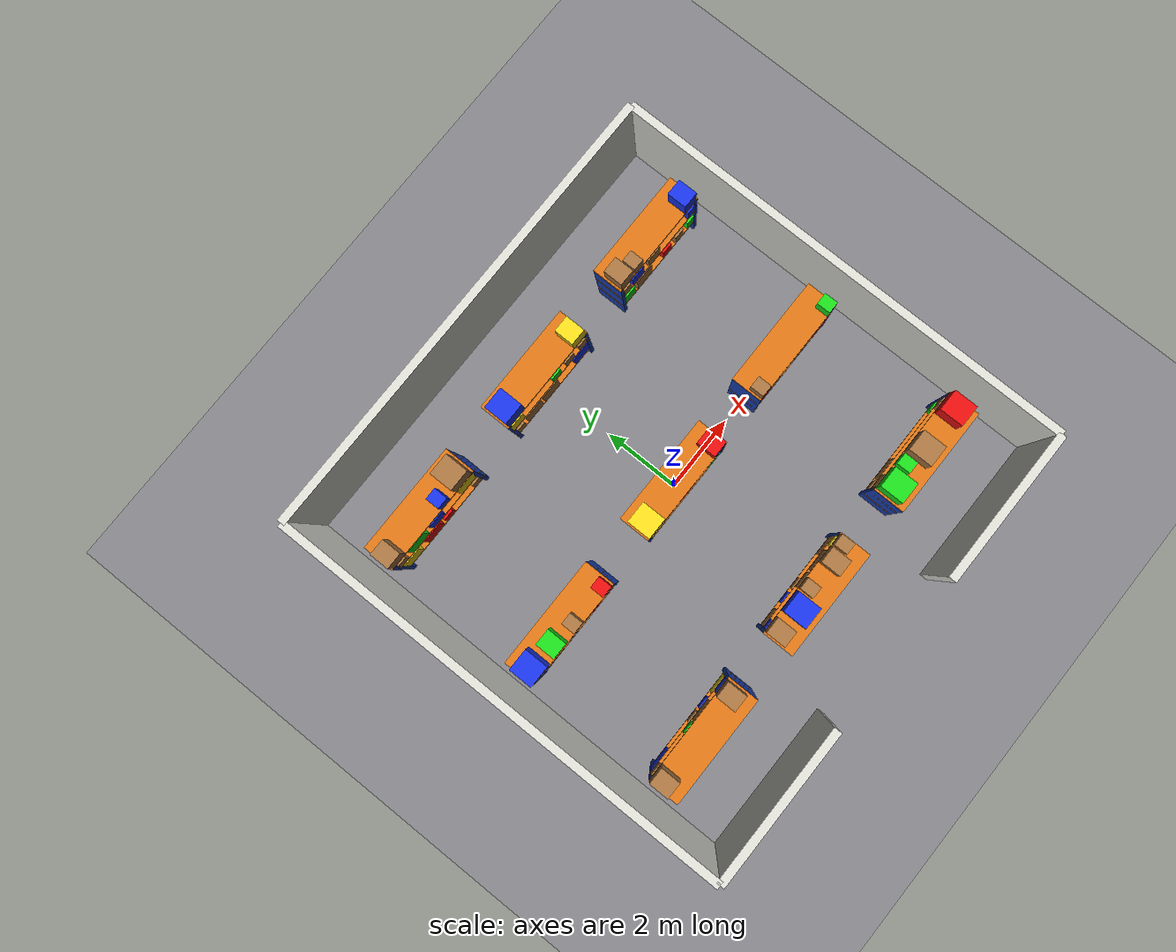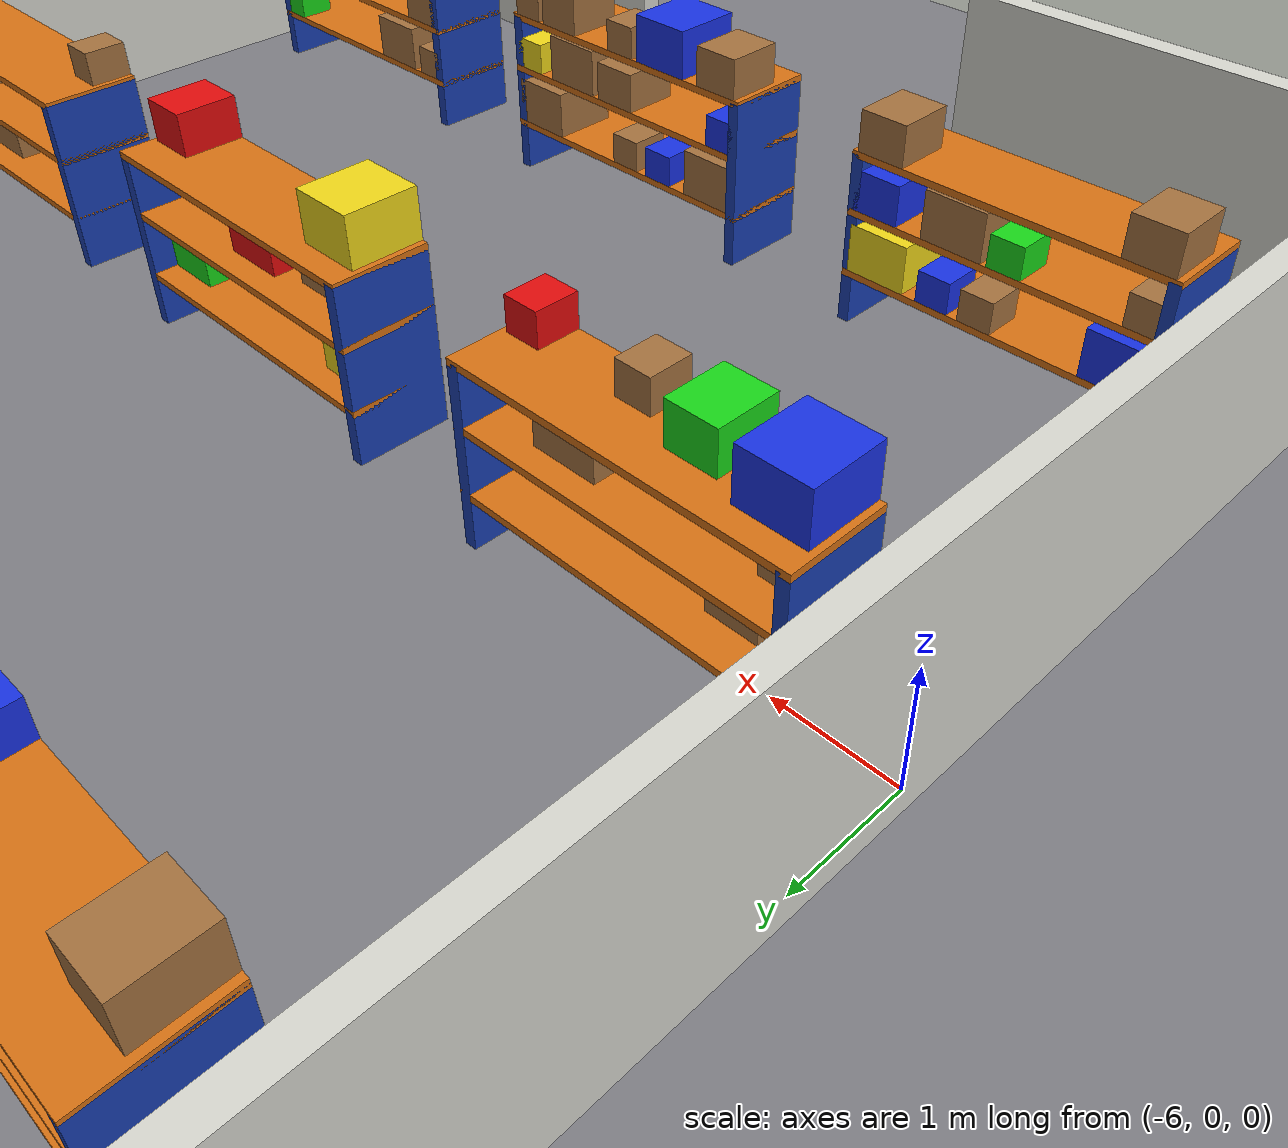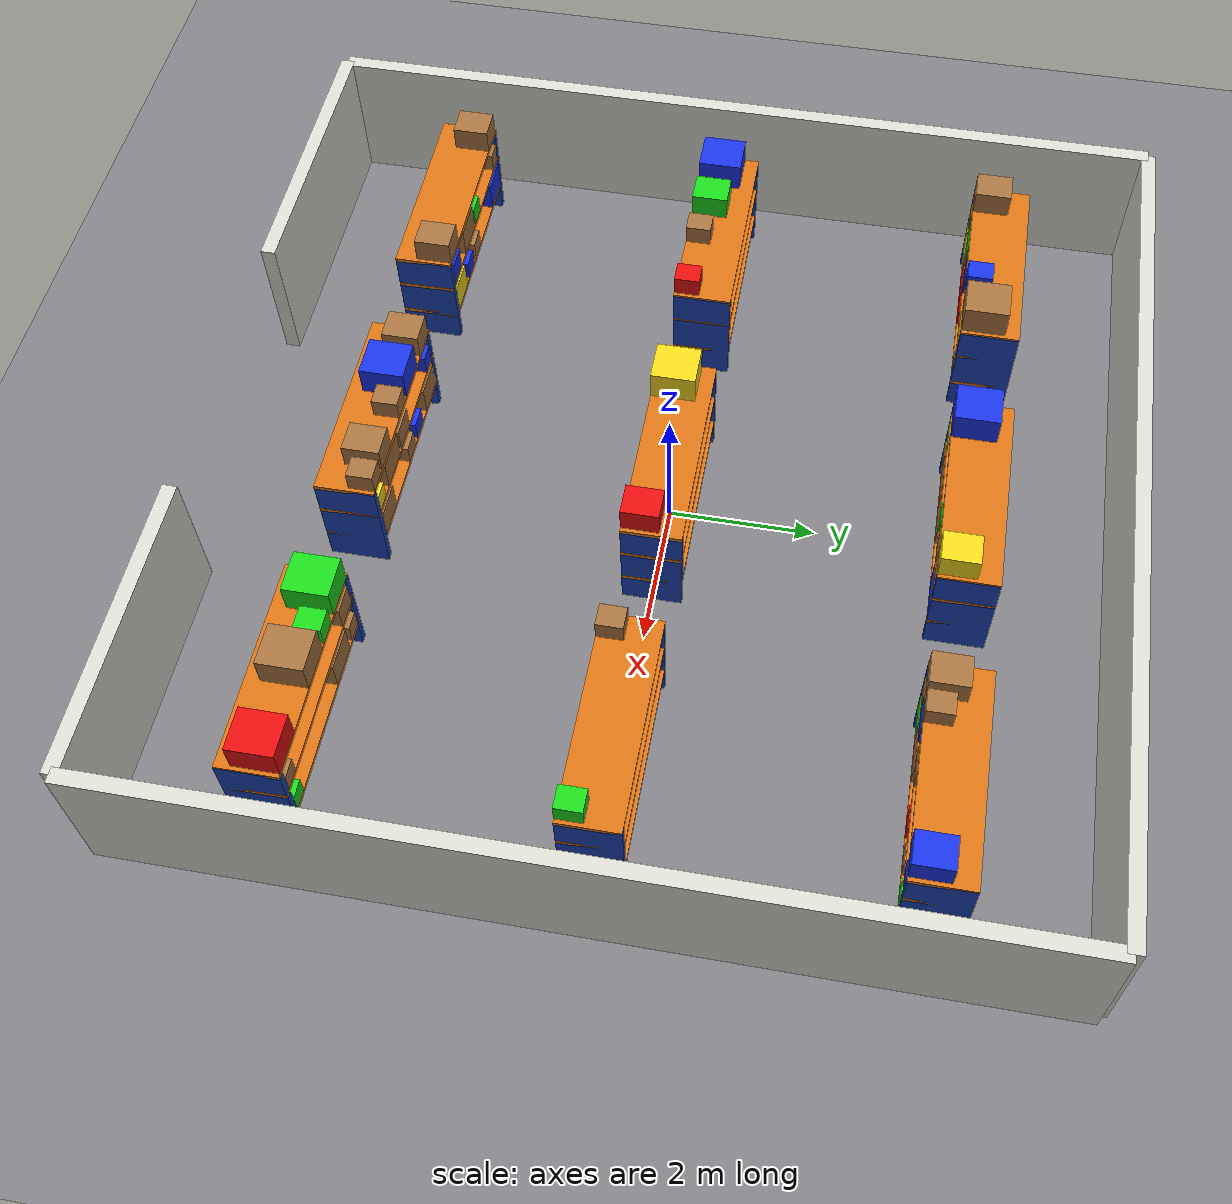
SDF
<?xml version="1.0" ?>
<sdf version="1.8">
  <world name="default">

    <physics name="1ms" type="ignored">
      <max_step_size>0.001</max_step_size>
      <real_time_factor>1.0</real_time_factor>
    </physics>

    <plugin filename="gz-sim-physics-system"
            name="gz::sim::systems::Physics"/>
    <plugin filename="gz-sim-user-commands-system"
            name="gz::sim::systems::UserCommands"/>
    <plugin filename="gz-sim-scene-broadcaster-system"
            name="gz::sim::systems::SceneBroadcaster"/>
    <plugin filename="gz-sim-sensors-system"
            name="gz::sim::systems::Sensors">
      <render_engine>ogre2</render_engine>
    </plugin>
    <plugin filename="gz-sim-imu-system"
            name="gz::sim::systems::Imu"/>

    <light type="directional" name="gunes">
      <cast_shadows>true</cast_shadows>
      <pose>0 0 10 0 0 0</pose>
      <diffuse>0.9 0.9 0.9 1</diffuse>
      <specular>0.3 0.3 0.3 1</specular>
      <direction>-0.3 0.2 -0.9</direction>
    </light>

    <model name="zemin">
      <static>true</static>
      <link name="link">
        <collision name="collision">
          <geometry>
            <plane>
              <normal>0 0 1</normal>
              <size>20 20</size>
            </plane>
          </geometry>
        </collision>
        <visual name="visual">
          <geometry>
            <plane>
              <normal>0 0 1</normal>
              <size>20 20</size>
            </plane>
          </geometry>
          <material>
            <ambient>0.4 0.4 0.42 1</ambient>
            <diffuse>0.5 0.5 0.52 1</diffuse>
          </material>
        </visual>
      </link>
    </model>

    <model name="duvarlar">
      <static>true</static>
      <link name="link">

        <collision name="kuzey_c">
          <pose>0 6 1 0 0 0</pose>
          <geometry><box><size>12 0.2 2</size></box></geometry>
        </collision>
        <visual name="kuzey_v">
          <pose>0 6 1 0 0 0</pose>
          <geometry><box><size>12 0.2 2</size></box></geometry>
          <material>
            <ambient>0.75 0.75 0.72 1</ambient>
            <diffuse>0.85 0.85 0.82 1</diffuse>
          </material>
        </visual>

        <collision name="guney_sol_c">
          <pose>-4 -6 1 0 0 0</pose>
          <geometry><box><size>4 0.2 2</size></box></geometry>
        </collision>
        <visual name="guney_sol_v">
          <pose>-4 -6 1 0 0 0</pose>
          <geometry><box><size>4 0.2 2</size></box></geometry>
          <material>
            <ambient>0.75 0.75 0.72 1</ambient>
            <diffuse>0.85 0.85 0.82 1</diffuse>
          </material>
        </visual>

        <collision name="guney_sag_c">
          <pose>4 -6 1 0 0 0</pose>
          <geometry><box><size>4 0.2 2</size></box></geometry>
        </collision>
        <visual name="guney_sag_v">
          <pose>4 -6 1 0 0 0</pose>
          <geometry><box><size>4 0.2 2</size></box></geometry>
          <material>
            <ambient>0.75 0.75 0.72 1</ambient>
            <diffuse>0.85 0.85 0.82 1</diffuse>
          </material>
        </visual>

        <collision name="dogu_c">
          <pose>6 0 1 0 0 0</pose>
          <geometry><box><size>0.2 12 2</size></box></geometry>
        </collision>
        <visual name="dogu_v">
          <pose>6 0 1 0 0 0</pose>
          <geometry><box><size>0.2 12 2</size></box></geometry>
          <material>
            <ambient>0.75 0.75 0.72 1</ambient>
            <diffuse>0.85 0.85 0.82 1</diffuse>
          </material>
        </visual>

        <collision name="bati_c">
          <pose>-6 0 1 0 0 0</pose>
          <geometry><box><size>0.2 12 2</size></box></geometry>
        </collision>
        <visual name="bati_v">
          <pose>-6 0 1 0 0 0</pose>
          <geometry><box><size>0.2 12 2</size></box></geometry>
          <material>
            <ambient>0.75 0.75 0.72 1</ambient>
            <diffuse>0.85 0.85 0.82 1</diffuse>
          </material>
        </visual>

      </link>
    </model>

    <model name="raf_A1">
      <static>true</static>
      <pose>-4 4 0 0 0 0</pose>
      <link name="link">

        <collision name="c">
          <pose>0 0 0.75 0 0 0</pose>
          <geometry><box><size>2.8 0.8 1.5</size></box></geometry>
        </collision>

        <visual name="lidar_dolgu">
          <pose>0 0 0.75 0 0 0</pose>
          <geometry><box><size>2.8 0.8 1.5</size></box></geometry>
          <transparency>1</transparency>
          <cast_shadows>false</cast_shadows>
        </visual>

        <visual name="dikey_sol">
          <pose>-1.35 0 0.75 0 0 0</pose>
          <geometry><box><size>0.1 0.8 1.5</size></box></geometry>
          <material>
            <ambient>0.05 0.15 0.5 1</ambient>
            <diffuse>0.1 0.25 0.7 1</diffuse>
          </material>
        </visual>

        <visual name="dikey_sag">
          <pose>1.35 0 0.75 0 0 0</pose>
          <geometry><box><size>0.1 0.8 1.5</size></box></geometry>
          <material>
            <ambient>0.05 0.15 0.5 1</ambient>
            <diffuse>0.1 0.25 0.7 1</diffuse>
          </material>
        </visual>

        <visual name="kat_1">
          <pose>0 0 0.45 0 0 0</pose>
          <geometry><box><size>2.8 0.8 0.06</size></box></geometry>
          <material>
            <ambient>0.6 0.3 0.05 1</ambient>
            <diffuse>0.85 0.45 0.08 1</diffuse>
          </material>
        </visual>

        <visual name="kat_2">
          <pose>0 0 1.0 0 0 0</pose>
          <geometry><box><size>2.8 0.8 0.06</size></box></geometry>
          <material>
            <ambient>0.6 0.3 0.05 1</ambient>
            <diffuse>0.85 0.45 0.08 1</diffuse>
          </material>
        </visual>

        <visual name="kat_3">
          <pose>0 0 1.5 0 0 0</pose>
          <geometry><box><size>2.8 0.8 0.06</size></box></geometry>
          <material>
            <ambient>0.6 0.3 0.05 1</ambient>
            <diffuse>0.85 0.45 0.08 1</diffuse>
          </material>
        </visual>

      </link>
    </model>

    <model name="raf_A2">
      <static>true</static>
      <pose>0 4 0 0 0 0</pose>
      <link name="link">

        <collision name="c">
          <pose>0 0 0.75 0 0 0</pose>
          <geometry><box><size>2.8 0.8 1.5</size></box></geometry>
        </collision>

        <visual name="lidar_dolgu">
          <pose>0 0 0.75 0 0 0</pose>
          <geometry><box><size>2.8 0.8 1.5</size></box></geometry>
          <transparency>1</transparency>
          <cast_shadows>false</cast_shadows>
        </visual>

        <visual name="dikey_sol">
          <pose>-1.35 0 0.75 0 0 0</pose>
          <geometry><box><size>0.1 0.8 1.5</size></box></geometry>
          <material>
            <ambient>0.05 0.15 0.5 1</ambient>
            <diffuse>0.1 0.25 0.7 1</diffuse>
          </material>
        </visual>

        <visual name="dikey_sag">
          <pose>1.35 0 0.75 0 0 0</pose>
          <geometry><box><size>0.1 0.8 1.5</size></box></geometry>
          <material>
            <ambient>0.05 0.15 0.5 1</ambient>
            <diffuse>0.1 0.25 0.7 1</diffuse>
          </material>
        </visual>

        <visual name="kat_1">
          <pose>0 0 0.45 0 0 0</pose>
          <geometry><box><size>2.8 0.8 0.06</size></box></geometry>
          <material>
            <ambient>0.6 0.3 0.05 1</ambient>
            <diffuse>0.85 0.45 0.08 1</diffuse>
          </material>
        </visual>

        <visual name="kat_2">
          <pose>0 0 1.0 0 0 0</pose>
          <geometry><box><size>2.8 0.8 0.06</size></box></geometry>
          <material>
            <ambient>0.6 0.3 0.05 1</ambient>
            <diffuse>0.85 0.45 0.08 1</diffuse>
          </material>
        </visual>

        <visual name="kat_3">
          <pose>0 0 1.5 0 0 0</pose>
          <geometry><box><size>2.8 0.8 0.06</size></box></geometry>
          <material>
            <ambient>0.6 0.3 0.05 1</ambient>
            <diffuse>0.85 0.45 0.08 1</diffuse>
          </material>
        </visual>

      </link>
    </model>

    <model name="raf_A3">
      <static>true</static>
      <pose>4 4 0 0 0 0</pose>
      <link name="link">

        <collision name="c">
          <pose>0 0 0.75 0 0 0</pose>
          <geometry><box><size>2.8 0.8 1.5</size></box></geometry>
        </collision>

        <visual name="lidar_dolgu">
          <pose>0 0 0.75 0 0 0</pose>
          <geometry><box><size>2.8 0.8 1.5</size></box></geometry>
          <transparency>1</transparency>
          <cast_shadows>false</cast_shadows>
        </visual>

        <visual name="dikey_sol">
          <pose>-1.35 0 0.75 0 0 0</pose>
          <geometry><box><size>0.1 0.8 1.5</size></box></geometry>
          <material>
            <ambient>0.05 0.15 0.5 1</ambient>
            <diffuse>0.1 0.25 0.7 1</diffuse>
          </material>
        </visual>

        <visual name="dikey_sag">
          <pose>1.35 0 0.75 0 0 0</pose>
          <geometry><box><size>0.1 0.8 1.5</size></box></geometry>
          <material>
            <ambient>0.05 0.15 0.5 1</ambient>
            <diffuse>0.1 0.25 0.7 1</diffuse>
          </material>
        </visual>

        <visual name="kat_1">
          <pose>0 0 0.45 0 0 0</pose>
          <geometry><box><size>2.8 0.8 0.06</size></box></geometry>
          <material>
            <ambient>0.6 0.3 0.05 1</ambient>
            <diffuse>0.85 0.45 0.08 1</diffuse>
          </material>
        </visual>

        <visual name="kat_2">
          <pose>0 0 1.0 0 0 0</pose>
          <geometry><box><size>2.8 0.8 0.06</size></box></geometry>
          <material>
            <ambient>0.6 0.3 0.05 1</ambient>
            <diffuse>0.85 0.45 0.08 1</diffuse>
          </material>
        </visual>

        <visual name="kat_3">
          <pose>0 0 1.5 0 0 0</pose>
          <geometry><box><size>2.8 0.8 0.06</size></box></geometry>
          <material>
            <ambient>0.6 0.3 0.05 1</ambient>
            <diffuse>0.85 0.45 0.08 1</diffuse>
          </material>
        </visual>

      </link>
    </model>

    <model name="raf_B1">
      <static>true</static>
      <pose>-4 0 0 0 0 0</pose>
      <link name="link">

        <collision name="c">
          <pose>0 0 0.75 0 0 0</pose>
          <geometry><box><size>2.8 0.8 1.5</size></box></geometry>
        </collision>

        <visual name="lidar_dolgu">
          <pose>0 0 0.75 0 0 0</pose>
          <geometry><box><size>2.8 0.8 1.5</size></box></geometry>
          <transparency>1</transparency>
          <cast_shadows>false</cast_shadows>
        </visual>

        <visual name="dikey_sol">
          <pose>-1.35 0 0.75 0 0 0</pose>
          <geometry><box><size>0.1 0.8 1.5</size></box></geometry>
          <material>
            <ambient>0.05 0.15 0.5 1</ambient>
            <diffuse>0.1 0.25 0.7 1</diffuse>
          </material>
        </visual>

        <visual name="dikey_sag">
          <pose>1.35 0 0.75 0 0 0</pose>
          <geometry><box><size>0.1 0.8 1.5</size></box></geometry>
          <material>
            <ambient>0.05 0.15 0.5 1</ambient>
            <diffuse>0.1 0.25 0.7 1</diffuse>
          </material>
        </visual>

        <visual name="kat_1">
          <pose>0 0 0.45 0 0 0</pose>
          <geometry><box><size>2.8 0.8 0.06</size></box></geometry>
          <material>
            <ambient>0.6 0.3 0.05 1</ambient>
            <diffuse>0.85 0.45 0.08 1</diffuse>
          </material>
        </visual>

        <visual name="kat_2">
          <pose>0 0 1.0 0 0 0</pose>
          <geometry><box><size>2.8 0.8 0.06</size></box></geometry>
          <material>
            <ambient>0.6 0.3 0.05 1</ambient>
            <diffuse>0.85 0.45 0.08 1</diffuse>
          </material>
        </visual>

        <visual name="kat_3">
          <pose>0 0 1.5 0 0 0</pose>
          <geometry><box><size>2.8 0.8 0.06</size></box></geometry>
          <material>
            <ambient>0.6 0.3 0.05 1</ambient>
            <diffuse>0.85 0.45 0.08 1</diffuse>
          </material>
        </visual>

      </link>
    </model>

    <model name="raf_B2">
      <static>true</static>
      <pose>0 0 0 0 0 0</pose>
      <link name="link">

        <collision name="c">
          <pose>0 0 0.75 0 0 0</pose>
          <geometry><box><size>2.8 0.8 1.5</size></box></geometry>
        </collision>

        <visual name="lidar_dolgu">
          <pose>0 0 0.75 0 0 0</pose>
          <geometry><box><size>2.8 0.8 1.5</size></box></geometry>
          <transparency>1</transparency>
          <cast_shadows>false</cast_shadows>
        </visual>

        <visual name="dikey_sol">
          <pose>-1.35 0 0.75 0 0 0</pose>
          <geometry><box><size>0.1 0.8 1.5</size></box></geometry>
          <material>
            <ambient>0.05 0.15 0.5 1</ambient>
            <diffuse>0.1 0.25 0.7 1</diffuse>
          </material>
        </visual>

        <visual name="dikey_sag">
          <pose>1.35 0 0.75 0 0 0</pose>
          <geometry><box><size>0.1 0.8 1.5</size></box></geometry>
          <material>
            <ambient>0.05 0.15 0.5 1</ambient>
            <diffuse>0.1 0.25 0.7 1</diffuse>
          </material>
        </visual>

        <visual name="kat_1">
          <pose>0 0 0.45 0 0 0</pose>
          <geometry><box><size>2.8 0.8 0.06</size></box></geometry>
          <material>
            <ambient>0.6 0.3 0.05 1</ambient>
            <diffuse>0.85 0.45 0.08 1</diffuse>
          </material>
        </visual>

        <visual name="kat_2">
          <pose>0 0 1.0 0 0 0</pose>
          <geometry><box><size>2.8 0.8 0.06</size></box></geometry>
          <material>
            <ambient>0.6 0.3 0.05 1</ambient>
            <diffuse>0.85 0.45 0.08 1</diffuse>
          </material>
        </visual>

        <visual name="kat_3">
          <pose>0 0 1.5 0 0 0</pose>
          <geometry><box><size>2.8 0.8 0.06</size></box></geometry>
          <material>
            <ambient>0.6 0.3 0.05 1</ambient>
            <diffuse>0.85 0.45 0.08 1</diffuse>
          </material>
        </visual>

      </link>
    </model>

    <model name="raf_B3">
      <static>true</static>
      <pose>4 0 0 0 0 0</pose>
      <link name="link">

        <collision name="c">
          <pose>0 0 0.75 0 0 0</pose>
          <geometry><box><size>2.8 0.8 1.5</size></box></geometry>
        </collision>

        <visual name="lidar_dolgu">
          <pose>0 0 0.75 0 0 0</pose>
          <geometry><box><size>2.8 0.8 1.5</size></box></geometry>
          <transparency>1</transparency>
          <cast_shadows>false</cast_shadows>
        </visual>

        <visual name="dikey_sol">
          <pose>-1.35 0 0.75 0 0 0</pose>
          <geometry><box><size>0.1 0.8 1.5</size></box></geometry>
          <material>
            <ambient>0.05 0.15 0.5 1</ambient>
            <diffuse>0.1 0.25 0.7 1</diffuse>
          </material>
        </visual>

        <visual name="dikey_sag">
          <pose>1.35 0 0.75 0 0 0</pose>
          <geometry><box><size>0.1 0.8 1.5</size></box></geometry>
          <material>
            <ambient>0.05 0.15 0.5 1</ambient>
            <diffuse>0.1 0.25 0.7 1</diffuse>
          </material>
        </visual>

        <visual name="kat_1">
          <pose>0 0 0.45 0 0 0</pose>
          <geometry><box><size>2.8 0.8 0.06</size></box></geometry>
          <material>
            <ambient>0.6 0.3 0.05 1</ambient>
            <diffuse>0.85 0.45 0.08 1</diffuse>
          </material>
        </visual>

        <visual name="kat_2">
          <pose>0 0 1.0 0 0 0</pose>
          <geometry><box><size>2.8 0.8 0.06</size></box></geometry>
          <material>
            <ambient>0.6 0.3 0.05 1</ambient>
            <diffuse>0.85 0.45 0.08 1</diffuse>
          </material>
        </visual>

        <visual name="kat_3">
          <pose>0 0 1.5 0 0 0</pose>
          <geometry><box><size>2.8 0.8 0.06</size></box></geometry>
          <material>
            <ambient>0.6 0.3 0.05 1</ambient>
            <diffuse>0.85 0.45 0.08 1</diffuse>
          </material>
        </visual>

      </link>
    </model>

    <model name="raf_C1">
      <static>true</static>
      <pose>-4 -4 0 0 0 0</pose>
      <link name="link">

        <collision name="c">
          <pose>0 0 0.75 0 0 0</pose>
          <geometry><box><size>2.8 0.8 1.5</size></box></geometry>
        </collision>

        <visual name="lidar_dolgu">
          <pose>0 0 0.75 0 0 0</pose>
          <geometry><box><size>2.8 0.8 1.5</size></box></geometry>
          <transparency>1</transparency>
          <cast_shadows>false</cast_shadows>
        </visual>

        <visual name="dikey_sol">
          <pose>-1.35 0 0.75 0 0 0</pose>
          <geometry><box><size>0.1 0.8 1.5</size></box></geometry>
          <material>
            <ambient>0.05 0.15 0.5 1</ambient>
            <diffuse>0.1 0.25 0.7 1</diffuse>
          </material>
        </visual>

        <visual name="dikey_sag">
          <pose>1.35 0 0.75 0 0 0</pose>
          <geometry><box><size>0.1 0.8 1.5</size></box></geometry>
          <material>
            <ambient>0.05 0.15 0.5 1</ambient>
            <diffuse>0.1 0.25 0.7 1</diffuse>
          </material>
        </visual>

        <visual name="kat_1">
          <pose>0 0 0.45 0 0 0</pose>
          <geometry><box><size>2.8 0.8 0.06</size></box></geometry>
          <material>
            <ambient>0.6 0.3 0.05 1</ambient>
            <diffuse>0.85 0.45 0.08 1</diffuse>
          </material>
        </visual>

        <visual name="kat_2">
          <pose>0 0 1.0 0 0 0</pose>
          <geometry><box><size>2.8 0.8 0.06</size></box></geometry>
          <material>
            <ambient>0.6 0.3 0.05 1</ambient>
            <diffuse>0.85 0.45 0.08 1</diffuse>
          </material>
        </visual>

        <visual name="kat_3">
          <pose>0 0 1.5 0 0 0</pose>
          <geometry><box><size>2.8 0.8 0.06</size></box></geometry>
          <material>
            <ambient>0.6 0.3 0.05 1</ambient>
            <diffuse>0.85 0.45 0.08 1</diffuse>
          </material>
        </visual>

      </link>
    </model>

    <model name="raf_C2">
      <static>true</static>
      <pose>0 -4 0 0 0 0</pose>
      <link name="link">

        <collision name="c">
          <pose>0 0 0.75 0 0 0</pose>
          <geometry><box><size>2.8 0.8 1.5</size></box></geometry>
        </collision>

        <visual name="lidar_dolgu">
          <pose>0 0 0.75 0 0 0</pose>
          <geometry><box><size>2.8 0.8 1.5</size></box></geometry>
          <transparency>1</transparency>
          <cast_shadows>false</cast_shadows>
        </visual>

        <visual name="dikey_sol">
          <pose>-1.35 0 0.75 0 0 0</pose>
          <geometry><box><size>0.1 0.8 1.5</size></box></geometry>
          <material>
            <ambient>0.05 0.15 0.5 1</ambient>
            <diffuse>0.1 0.25 0.7 1</diffuse>
          </material>
        </visual>

        <visual name="dikey_sag">
          <pose>1.35 0 0.75 0 0 0</pose>
          <geometry><box><size>0.1 0.8 1.5</size></box></geometry>
          <material>
            <ambient>0.05 0.15 0.5 1</ambient>
            <diffuse>0.1 0.25 0.7 1</diffuse>
          </material>
        </visual>

        <visual name="kat_1">
          <pose>0 0 0.45 0 0 0</pose>
          <geometry><box><size>2.8 0.8 0.06</size></box></geometry>
          <material>
            <ambient>0.6 0.3 0.05 1</ambient>
            <diffuse>0.85 0.45 0.08 1</diffuse>
          </material>
        </visual>

        <visual name="kat_2">
          <pose>0 0 1.0 0 0 0</pose>
          <geometry><box><size>2.8 0.8 0.06</size></box></geometry>
          <material>
            <ambient>0.6 0.3 0.05 1</ambient>
            <diffuse>0.85 0.45 0.08 1</diffuse>
          </material>
        </visual>

        <visual name="kat_3">
          <pose>0 0 1.5 0 0 0</pose>
          <geometry><box><size>2.8 0.8 0.06</size></box></geometry>
          <material>
            <ambient>0.6 0.3 0.05 1</ambient>
            <diffuse>0.85 0.45 0.08 1</diffuse>
          </material>
        </visual>

      </link>
    </model>

    <model name="raf_C3">
      <static>true</static>
      <pose>4 -4 0 0 0 0</pose>
      <link name="link">

        <collision name="c">
          <pose>0 0 0.75 0 0 0</pose>
          <geometry><box><size>2.8 0.8 1.5</size></box></geometry>
        </collision>

        <visual name="lidar_dolgu">
          <pose>0 0 0.75 0 0 0</pose>
          <geometry><box><size>2.8 0.8 1.5</size></box></geometry>
          <transparency>1</transparency>
          <cast_shadows>false</cast_shadows>
        </visual>

        <visual name="dikey_sol">
          <pose>-1.35 0 0.75 0 0 0</pose>
          <geometry><box><size>0.1 0.8 1.5</size></box></geometry>
          <material>
            <ambient>0.05 0.15 0.5 1</ambient>
            <diffuse>0.1 0.25 0.7 1</diffuse>
          </material>
        </visual>

        <visual name="dikey_sag">
          <pose>1.35 0 0.75 0 0 0</pose>
          <geometry><box><size>0.1 0.8 1.5</size></box></geometry>
          <material>
            <ambient>0.05 0.15 0.5 1</ambient>
            <diffuse>0.1 0.25 0.7 1</diffuse>
          </material>
        </visual>

        <visual name="kat_1">
          <pose>0 0 0.45 0 0 0</pose>
          <geometry><box><size>2.8 0.8 0.06</size></box></geometry>
          <material>
            <ambient>0.6 0.3 0.05 1</ambient>
            <diffuse>0.85 0.45 0.08 1</diffuse>
          </material>
        </visual>

        <visual name="kat_2">
          <pose>0 0 1.0 0 0 0</pose>
          <geometry><box><size>2.8 0.8 0.06</size></box></geometry>
          <material>
            <ambient>0.6 0.3 0.05 1</ambient>
            <diffuse>0.85 0.45 0.08 1</diffuse>
          </material>
        </visual>

        <visual name="kat_3">
          <pose>0 0 1.5 0 0 0</pose>
          <geometry><box><size>2.8 0.8 0.06</size></box></geometry>
          <material>
            <ambient>0.6 0.3 0.05 1</ambient>
            <diffuse>0.85 0.45 0.08 1</diffuse>
          </material>
        </visual>

      </link>
    </model>

    <!-- OTOMATIK URETILDI: kutu_uret.py -->
    <model name="kutu_A1_k1_p1">
      <static>true</static>
      <pose>-5.075 3.900 0.690 0 0 0</pose>
      <link name="link">
        <collision name="c">
          <geometry><box><size>0.55 0.60 0.42</size></box></geometry>
        </collision>
        <visual name="v">
          <geometry><box><size>0.55 0.60 0.42</size></box></geometry>
          <material>
            <ambient>0.7 0.6 0.05 1</ambient>
            <diffuse>0.95 0.85 0.1 1</diffuse>
            <specular>0.1 0.1 0.1 1</specular>
          </material>
        </visual>
      </link>
    </model>
    <model name="kutu_A1_k1_p2">
      <static>true</static>
      <pose>-4.327 3.900 0.690 0 0 0</pose>
      <link name="link">
        <collision name="c">
          <geometry><box><size>0.55 0.60 0.42</size></box></geometry>
        </collision>
        <visual name="v">
          <geometry><box><size>0.55 0.60 0.42</size></box></geometry>
          <material>
            <ambient>0.6 0.02 0.02 1</ambient>
            <diffuse>0.9 0.05 0.05 1</diffuse>
            <specular>0.1 0.1 0.1 1</specular>
          </material>
        </visual>
      </link>
    </model>
    <model name="kutu_A1_k1_p3">
      <static>true</static>
      <pose>-3.807 3.775 0.620 0 0 0</pose>
      <link name="link">
        <collision name="c">
          <geometry><box><size>0.30 0.35 0.28</size></box></geometry>
        </collision>
        <visual name="v">
          <geometry><box><size>0.30 0.35 0.28</size></box></geometry>
          <material>
            <ambient>0.6 0.02 0.02 1</ambient>
            <diffuse>0.9 0.05 0.05 1</diffuse>
            <specular>0.1 0.1 0.1 1</specular>
          </material>
        </visual>
      </link>
    </model>
    <model name="kutu_A1_k1_p4">
      <static>true</static>
      <pose>-2.800 3.775 0.620 0 0 0</pose>
      <link name="link">
        <collision name="c">
          <geometry><box><size>0.30 0.35 0.28</size></box></geometry>
        </collision>
        <visual name="v">
          <geometry><box><size>0.30 0.35 0.28</size></box></geometry>
          <material>
            <ambient>0.4 0.28 0.15 1</ambient>
            <diffuse>0.65 0.45 0.25 1</diffuse>
            <specular>0.1 0.1 0.1 1</specular>
          </material>
        </visual>
      </link>
    </model>
    <model name="kutu_A1_k2_p1">
      <static>true</static>
      <pose>-5.200 3.775 1.170 0 0 0</pose>
      <link name="link">
        <collision name="c">
          <geometry><box><size>0.30 0.35 0.28</size></box></geometry>
        </collision>
        <visual name="v">
          <geometry><box><size>0.30 0.35 0.28</size></box></geometry>
          <material>
            <ambient>0.4 0.28 0.15 1</ambient>
            <diffuse>0.65 0.45 0.25 1</diffuse>
            <specular>0.1 0.1 0.1 1</specular>
          </material>
        </visual>
      </link>
    </model>
    <model name="kutu_A1_k2_p2">
      <static>true</static>
      <pose>-4.616 3.900 1.240 0 0 0</pose>
      <link name="link">
        <collision name="c">
          <geometry><box><size>0.55 0.60 0.42</size></box></geometry>
        </collision>
        <visual name="v">
          <geometry><box><size>0.55 0.60 0.42</size></box></geometry>
          <material>
            <ambient>0.05 0.5 0.05 1</ambient>
            <diffuse>0.1 0.85 0.1 1</diffuse>
            <specular>0.1 0.1 0.1 1</specular>
          </material>
        </visual>
      </link>
    </model>
    <model name="kutu_A1_k2_p3">
      <static>true</static>
      <pose>-3.991 3.850 1.205 0 0 0</pose>
      <link name="link">
        <collision name="c">
          <geometry><box><size>0.42 0.50 0.35</size></box></geometry>
        </collision>
        <visual name="v">
          <geometry><box><size>0.42 0.50 0.35</size></box></geometry>
          <material>
            <ambient>0.05 0.1 0.6 1</ambient>
            <diffuse>0.1 0.2 0.9 1</diffuse>
            <specular>0.1 0.1 0.1 1</specular>
          </material>
        </visual>
      </link>
    </model>
    <model name="kutu_A1_k2_p4">
      <static>true</static>
      <pose>-2.925 3.900 1.240 0 0 0</pose>
      <link name="link">
        <collision name="c">
          <geometry><box><size>0.55 0.60 0.42</size></box></geometry>
        </collision>
        <visual name="v">
          <geometry><box><size>0.55 0.60 0.42</size></box></geometry>
          <material>
            <ambient>0.7 0.6 0.05 1</ambient>
            <diffuse>0.95 0.85 0.1 1</diffuse>
            <specular>0.1 0.1 0.1 1</specular>
          </material>
        </visual>
      </link>
    </model>
    <model name="kutu_A1_k3_p1">
      <static>true</static>
      <pose>-5.140 3.850 1.705 0 0 0</pose>
      <link name="link">
        <collision name="c">
          <geometry><box><size>0.42 0.50 0.35</size></box></geometry>
        </collision>
        <visual name="v">
          <geometry><box><size>0.42 0.50 0.35</size></box></geometry>
          <material>
            <ambient>0.4 0.28 0.15 1</ambient>
            <diffuse>0.65 0.45 0.25 1</diffuse>
            <specular>0.1 0.1 0.1 1</specular>
          </material>
        </visual>
      </link>
    </model>
    <model name="kutu_A1_k3_p2">
      <static>true</static>
      <pose>-3.546 3.775 1.670 0 0 0</pose>
      <link name="link">
        <collision name="c">
          <geometry><box><size>0.30 0.35 0.28</size></box></geometry>
        </collision>
        <visual name="v">
          <geometry><box><size>0.30 0.35 0.28</size></box></geometry>
          <material>
            <ambient>0.05 0.1 0.6 1</ambient>
            <diffuse>0.1 0.2 0.9 1</diffuse>
            <specular>0.1 0.1 0.1 1</specular>
          </material>
        </visual>
      </link>
    </model>
    <model name="kutu_A1_k3_p3">
      <static>true</static>
      <pose>-2.925 3.900 1.740 0 0 0</pose>
      <link name="link">
        <collision name="c">
          <geometry><box><size>0.55 0.60 0.42</size></box></geometry>
        </collision>
        <visual name="v">
          <geometry><box><size>0.55 0.60 0.42</size></box></geometry>
          <material>
            <ambient>0.4 0.28 0.15 1</ambient>
            <diffuse>0.65 0.45 0.25 1</diffuse>
            <specular>0.1 0.1 0.1 1</specular>
          </material>
        </visual>
      </link>
    </model>
    <model name="kutu_A2_k1_p1">
      <static>true</static>
      <pose>-1.200 3.775 0.620 0 0 0</pose>
      <link name="link">
        <collision name="c">
          <geometry><box><size>0.30 0.35 0.28</size></box></geometry>
        </collision>
        <visual name="v">
          <geometry><box><size>0.30 0.35 0.28</size></box></geometry>
          <material>
            <ambient>0.4 0.28 0.15 1</ambient>
            <diffuse>0.65 0.45 0.25 1</diffuse>
            <specular>0.1 0.1 0.1 1</specular>
          </material>
        </visual>
      </link>
    </model>
    <model name="kutu_A2_k1_p2">
      <static>true</static>
      <pose>-0.687 3.900 0.690 0 0 0</pose>
      <link name="link">
        <collision name="c">
          <geometry><box><size>0.55 0.60 0.42</size></box></geometry>
        </collision>
        <visual name="v">
          <geometry><box><size>0.55 0.60 0.42</size></box></geometry>
          <material>
            <ambient>0.4 0.28 0.15 1</ambient>
            <diffuse>0.65 0.45 0.25 1</diffuse>
            <specular>0.1 0.1 0.1 1</specular>
          </material>
        </visual>
      </link>
    </model>
    <model name="kutu_A2_k1_p3">
      <static>true</static>
      <pose>-0.077 3.900 0.690 0 0 0</pose>
      <link name="link">
        <collision name="c">
          <geometry><box><size>0.55 0.60 0.42</size></box></geometry>
        </collision>
        <visual name="v">
          <geometry><box><size>0.55 0.60 0.42</size></box></geometry>
          <material>
            <ambient>0.4 0.28 0.15 1</ambient>
            <diffuse>0.65 0.45 0.25 1</diffuse>
            <specular>0.1 0.1 0.1 1</specular>
          </material>
        </visual>
      </link>
    </model>
    <model name="kutu_A2_k1_p4">
      <static>true</static>
      <pose>1.075 3.900 0.690 0 0 0</pose>
      <link name="link">
        <collision name="c">
          <geometry><box><size>0.55 0.60 0.42</size></box></geometry>
        </collision>
        <visual name="v">
          <geometry><box><size>0.55 0.60 0.42</size></box></geometry>
          <material>
            <ambient>0.05 0.1 0.6 1</ambient>
            <diffuse>0.1 0.2 0.9 1</diffuse>
            <specular>0.1 0.1 0.1 1</specular>
          </material>
        </visual>
      </link>
    </model>
    <model name="kutu_A2_k2_p1">
      <static>true</static>
      <pose>-1.140 3.850 1.205 0 0 0</pose>
      <link name="link">
        <collision name="c">
          <geometry><box><size>0.42 0.50 0.35</size></box></geometry>
        </collision>
        <visual name="v">
          <geometry><box><size>0.42 0.50 0.35</size></box></geometry>
          <material>
            <ambient>0.7 0.6 0.05 1</ambient>
            <diffuse>0.95 0.85 0.1 1</diffuse>
            <specular>0.1 0.1 0.1 1</specular>
          </material>
        </visual>
      </link>
    </model>
    <model name="kutu_A2_k2_p2">
      <static>true</static>
      <pose>0.243 3.775 1.170 0 0 0</pose>
      <link name="link">
        <collision name="c">
          <geometry><box><size>0.30 0.35 0.28</size></box></geometry>
        </collision>
        <visual name="v">
          <geometry><box><size>0.30 0.35 0.28</size></box></geometry>
          <material>
            <ambient>0.05 0.5 0.05 1</ambient>
            <diffuse>0.1 0.85 0.1 1</diffuse>
            <specular>0.1 0.1 0.1 1</specular>
          </material>
        </visual>
      </link>
    </model>
    <model name="kutu_A2_k2_p3">
      <static>true</static>
      <pose>0.720 3.775 1.170 0 0 0</pose>
      <link name="link">
        <collision name="c">
          <geometry><box><size>0.30 0.35 0.28</size></box></geometry>
        </collision>
        <visual name="v">
          <geometry><box><size>0.30 0.35 0.28</size></box></geometry>
          <material>
            <ambient>0.4 0.28 0.15 1</ambient>
            <diffuse>0.65 0.45 0.25 1</diffuse>
            <specular>0.1 0.1 0.1 1</specular>
          </material>
        </visual>
      </link>
    </model>
    <model name="kutu_A2_k2_p4">
      <static>true</static>
      <pose>1.200 3.775 1.170 0 0 0</pose>
      <link name="link">
        <collision name="c">
          <geometry><box><size>0.30 0.35 0.28</size></box></geometry>
        </collision>
        <visual name="v">
          <geometry><box><size>0.30 0.35 0.28</size></box></geometry>
          <material>
            <ambient>0.4 0.28 0.15 1</ambient>
            <diffuse>0.65 0.45 0.25 1</diffuse>
            <specular>0.1 0.1 0.1 1</specular>
          </material>
        </visual>
      </link>
    </model>
    <model name="kutu_A2_k3_p1">
      <static>true</static>
      <pose>-1.075 3.900 1.740 0 0 0</pose>
      <link name="link">
        <collision name="c">
          <geometry><box><size>0.55 0.60 0.42</size></box></geometry>
        </collision>
        <visual name="v">
          <geometry><box><size>0.55 0.60 0.42</size></box></geometry>
          <material>
            <ambient>0.05 0.1 0.6 1</ambient>
            <diffuse>0.1 0.2 0.9 1</diffuse>
            <specular>0.1 0.1 0.1 1</specular>
          </material>
        </visual>
      </link>
    </model>
    <model name="kutu_A2_k3_p2">
      <static>true</static>
      <pose>1.140 3.850 1.705 0 0 0</pose>
      <link name="link">
        <collision name="c">
          <geometry><box><size>0.42 0.50 0.35</size></box></geometry>
        </collision>
        <visual name="v">
          <geometry><box><size>0.42 0.50 0.35</size></box></geometry>
          <material>
            <ambient>0.7 0.6 0.05 1</ambient>
            <diffuse>0.95 0.85 0.1 1</diffuse>
            <specular>0.1 0.1 0.1 1</specular>
          </material>
        </visual>
      </link>
    </model>
    <model name="kutu_A3_k1_p1">
      <static>true</static>
      <pose>2.860 3.850 0.655 0 0 0</pose>
      <link name="link">
        <collision name="c">
          <geometry><box><size>0.42 0.50 0.35</size></box></geometry>
        </collision>
        <visual name="v">
          <geometry><box><size>0.42 0.50 0.35</size></box></geometry>
          <material>
            <ambient>0.05 0.5 0.05 1</ambient>
            <diffuse>0.1 0.85 0.1 1</diffuse>
            <specular>0.1 0.1 0.1 1</specular>
          </material>
        </visual>
      </link>
    </model>
    <model name="kutu_A3_k1_p2">
      <static>true</static>
      <pose>3.424 3.900 0.690 0 0 0</pose>
      <link name="link">
        <collision name="c">
          <geometry><box><size>0.55 0.60 0.42</size></box></geometry>
        </collision>
        <visual name="v">
          <geometry><box><size>0.55 0.60 0.42</size></box></geometry>
          <material>
            <ambient>0.4 0.28 0.15 1</ambient>
            <diffuse>0.65 0.45 0.25 1</diffuse>
            <specular>0.1 0.1 0.1 1</specular>
          </material>
        </visual>
      </link>
    </model>
    <model name="kutu_A3_k1_p3">
      <static>true</static>
      <pose>4.275 3.775 0.620 0 0 0</pose>
      <link name="link">
        <collision name="c">
          <geometry><box><size>0.30 0.35 0.28</size></box></geometry>
        </collision>
        <visual name="v">
          <geometry><box><size>0.30 0.35 0.28</size></box></geometry>
          <material>
            <ambient>0.6 0.02 0.02 1</ambient>
            <diffuse>0.9 0.05 0.05 1</diffuse>
            <specular>0.1 0.1 0.1 1</specular>
          </material>
        </visual>
      </link>
    </model>
    <model name="kutu_A3_k1_p4">
      <static>true</static>
      <pose>4.742 3.775 0.620 0 0 0</pose>
      <link name="link">
        <collision name="c">
          <geometry><box><size>0.30 0.35 0.28</size></box></geometry>
        </collision>
        <visual name="v">
          <geometry><box><size>0.30 0.35 0.28</size></box></geometry>
          <material>
            <ambient>0.4 0.28 0.15 1</ambient>
            <diffuse>0.65 0.45 0.25 1</diffuse>
            <specular>0.1 0.1 0.1 1</specular>
          </material>
        </visual>
      </link>
    </model>
    <model name="kutu_A3_k1_p5">
      <static>true</static>
      <pose>5.200 3.775 0.620 0 0 0</pose>
      <link name="link">
        <collision name="c">
          <geometry><box><size>0.30 0.35 0.28</size></box></geometry>
        </collision>
        <visual name="v">
          <geometry><box><size>0.30 0.35 0.28</size></box></geometry>
          <material>
            <ambient>0.05 0.5 0.05 1</ambient>
            <diffuse>0.1 0.85 0.1 1</diffuse>
            <specular>0.1 0.1 0.1 1</specular>
          </material>
        </visual>
      </link>
    </model>
    <model name="kutu_A3_k2_p1">
      <static>true</static>
      <pose>2.800 3.775 1.170 0 0 0</pose>
      <link name="link">
        <collision name="c">
          <geometry><box><size>0.30 0.35 0.28</size></box></geometry>
        </collision>
        <visual name="v">
          <geometry><box><size>0.30 0.35 0.28</size></box></geometry>
          <material>
            <ambient>0.4 0.28 0.15 1</ambient>
            <diffuse>0.65 0.45 0.25 1</diffuse>
            <specular>0.1 0.1 0.1 1</specular>
          </material>
        </visual>
      </link>
    </model>
    <model name="kutu_A3_k2_p2">
      <static>true</static>
      <pose>3.223 3.850 1.205 0 0 0</pose>
      <link name="link">
        <collision name="c">
          <geometry><box><size>0.42 0.50 0.35</size></box></geometry>
        </collision>
        <visual name="v">
          <geometry><box><size>0.42 0.50 0.35</size></box></geometry>
          <material>
            <ambient>0.05 0.1 0.6 1</ambient>
            <diffuse>0.1 0.2 0.9 1</diffuse>
            <specular>0.1 0.1 0.1 1</specular>
          </material>
        </visual>
      </link>
    </model>
    <model name="kutu_A3_k2_p3">
      <static>true</static>
      <pose>3.812 3.850 1.205 0 0 0</pose>
      <link name="link">
        <collision name="c">
          <geometry><box><size>0.42 0.50 0.35</size></box></geometry>
        </collision>
        <visual name="v">
          <geometry><box><size>0.42 0.50 0.35</size></box></geometry>
          <material>
            <ambient>0.4 0.28 0.15 1</ambient>
            <diffuse>0.65 0.45 0.25 1</diffuse>
            <specular>0.1 0.1 0.1 1</specular>
          </material>
        </visual>
      </link>
    </model>
    <model name="kutu_A3_k2_p4">
      <static>true</static>
      <pose>5.200 3.775 1.170 0 0 0</pose>
      <link name="link">
        <collision name="c">
          <geometry><box><size>0.30 0.35 0.28</size></box></geometry>
        </collision>
        <visual name="v">
          <geometry><box><size>0.30 0.35 0.28</size></box></geometry>
          <material>
            <ambient>0.05 0.1 0.6 1</ambient>
            <diffuse>0.1 0.2 0.9 1</diffuse>
            <specular>0.1 0.1 0.1 1</specular>
          </material>
        </visual>
      </link>
    </model>
    <model name="kutu_A3_k3_p1">
      <static>true</static>
      <pose>2.860 3.850 1.705 0 0 0</pose>
      <link name="link">
        <collision name="c">
          <geometry><box><size>0.42 0.50 0.35</size></box></geometry>
        </collision>
        <visual name="v">
          <geometry><box><size>0.42 0.50 0.35</size></box></geometry>
          <material>
            <ambient>0.4 0.28 0.15 1</ambient>
            <diffuse>0.65 0.45 0.25 1</diffuse>
            <specular>0.1 0.1 0.1 1</specular>
          </material>
        </visual>
      </link>
    </model>
    <model name="kutu_A3_k3_p2">
      <static>true</static>
      <pose>3.271 3.775 1.670 0 0 0</pose>
      <link name="link">
        <collision name="c">
          <geometry><box><size>0.30 0.35 0.28</size></box></geometry>
        </collision>
        <visual name="v">
          <geometry><box><size>0.30 0.35 0.28</size></box></geometry>
          <material>
            <ambient>0.4 0.28 0.15 1</ambient>
            <diffuse>0.65 0.45 0.25 1</diffuse>
            <specular>0.1 0.1 0.1 1</specular>
          </material>
        </visual>
      </link>
    </model>
    <model name="kutu_A3_k3_p3">
      <static>true</static>
      <pose>5.140 3.850 1.705 0 0 0</pose>
      <link name="link">
        <collision name="c">
          <geometry><box><size>0.42 0.50 0.35</size></box></geometry>
        </collision>
        <visual name="v">
          <geometry><box><size>0.42 0.50 0.35</size></box></geometry>
          <material>
            <ambient>0.05 0.1 0.6 1</ambient>
            <diffuse>0.1 0.2 0.9 1</diffuse>
            <specular>0.1 0.1 0.1 1</specular>
          </material>
        </visual>
      </link>
    </model>
    <model name="kutu_B1_k1_p1">
      <static>true</static>
      <pose>-5.200 -0.225 0.620 0 0 0</pose>
      <link name="link">
        <collision name="c">
          <geometry><box><size>0.30 0.35 0.28</size></box></geometry>
        </collision>
        <visual name="v">
          <geometry><box><size>0.30 0.35 0.28</size></box></geometry>
          <material>
            <ambient>0.05 0.1 0.6 1</ambient>
            <diffuse>0.1 0.2 0.9 1</diffuse>
            <specular>0.1 0.1 0.1 1</specular>
          </material>
        </visual>
      </link>
    </model>
    <model name="kutu_B1_k1_p2">
      <static>true</static>
      <pose>-4.750 -0.150 0.655 0 0 0</pose>
      <link name="link">
        <collision name="c">
          <geometry><box><size>0.42 0.50 0.35</size></box></geometry>
        </collision>
        <visual name="v">
          <geometry><box><size>0.42 0.50 0.35</size></box></geometry>
          <material>
            <ambient>0.4 0.28 0.15 1</ambient>
            <diffuse>0.65 0.45 0.25 1</diffuse>
            <specular>0.1 0.1 0.1 1</specular>
          </material>
        </visual>
      </link>
    </model>
    <model name="kutu_B1_k1_p3">
      <static>true</static>
      <pose>-4.188 -0.225 0.620 0 0 0</pose>
      <link name="link">
        <collision name="c">
          <geometry><box><size>0.30 0.35 0.28</size></box></geometry>
        </collision>
        <visual name="v">
          <geometry><box><size>0.30 0.35 0.28</size></box></geometry>
          <material>
            <ambient>0.4 0.28 0.15 1</ambient>
            <diffuse>0.65 0.45 0.25 1</diffuse>
            <specular>0.1 0.1 0.1 1</specular>
          </material>
        </visual>
      </link>
    </model>
    <model name="kutu_B1_k1_p4">
      <static>true</static>
      <pose>-3.334 -0.225 0.620 0 0 0</pose>
      <link name="link">
        <collision name="c">
          <geometry><box><size>0.30 0.35 0.28</size></box></geometry>
        </collision>
        <visual name="v">
          <geometry><box><size>0.30 0.35 0.28</size></box></geometry>
          <material>
            <ambient>0.6 0.02 0.02 1</ambient>
            <diffuse>0.9 0.05 0.05 1</diffuse>
            <specular>0.1 0.1 0.1 1</specular>
          </material>
        </visual>
      </link>
    </model>
    <model name="kutu_B1_k1_p5">
      <static>true</static>
      <pose>-2.800 -0.225 0.620 0 0 0</pose>
      <link name="link">
        <collision name="c">
          <geometry><box><size>0.30 0.35 0.28</size></box></geometry>
        </collision>
        <visual name="v">
          <geometry><box><size>0.30 0.35 0.28</size></box></geometry>
          <material>
            <ambient>0.6 0.02 0.02 1</ambient>
            <diffuse>0.9 0.05 0.05 1</diffuse>
            <specular>0.1 0.1 0.1 1</specular>
          </material>
        </visual>
      </link>
    </model>
    <model name="kutu_B1_k2_p1">
      <static>true</static>
      <pose>-5.140 -0.150 1.205 0 0 0</pose>
      <link name="link">
        <collision name="c">
          <geometry><box><size>0.42 0.50 0.35</size></box></geometry>
        </collision>
        <visual name="v">
          <geometry><box><size>0.42 0.50 0.35</size></box></geometry>
          <material>
            <ambient>0.4 0.28 0.15 1</ambient>
            <diffuse>0.65 0.45 0.25 1</diffuse>
            <specular>0.1 0.1 0.1 1</specular>
          </material>
        </visual>
      </link>
    </model>
    <model name="kutu_B1_k2_p2">
      <static>true</static>
      <pose>-4.035 -0.225 1.170 0 0 0</pose>
      <link name="link">
        <collision name="c">
          <geometry><box><size>0.30 0.35 0.28</size></box></geometry>
        </collision>
        <visual name="v">
          <geometry><box><size>0.30 0.35 0.28</size></box></geometry>
          <material>
            <ambient>0.4 0.28 0.15 1</ambient>
            <diffuse>0.65 0.45 0.25 1</diffuse>
            <specular>0.1 0.1 0.1 1</specular>
          </material>
        </visual>
      </link>
    </model>
    <model name="kutu_B1_k2_p3">
      <static>true</static>
      <pose>-3.428 -0.100 1.240 0 0 0</pose>
      <link name="link">
        <collision name="c">
          <geometry><box><size>0.55 0.60 0.42</size></box></geometry>
        </collision>
        <visual name="v">
          <geometry><box><size>0.55 0.60 0.42</size></box></geometry>
          <material>
            <ambient>0.4 0.28 0.15 1</ambient>
            <diffuse>0.65 0.45 0.25 1</diffuse>
            <specular>0.1 0.1 0.1 1</specular>
          </material>
        </visual>
      </link>
    </model>
    <model name="kutu_B1_k2_p4">
      <static>true</static>
      <pose>-2.800 -0.225 1.170 0 0 0</pose>
      <link name="link">
        <collision name="c">
          <geometry><box><size>0.30 0.35 0.28</size></box></geometry>
        </collision>
        <visual name="v">
          <geometry><box><size>0.30 0.35 0.28</size></box></geometry>
          <material>
            <ambient>0.4 0.28 0.15 1</ambient>
            <diffuse>0.65 0.45 0.25 1</diffuse>
            <specular>0.1 0.1 0.1 1</specular>
          </material>
        </visual>
      </link>
    </model>
    <model name="kutu_B1_k3_p1">
      <static>true</static>
      <pose>-5.075 -0.100 1.740 0 0 0</pose>
      <link name="link">
        <collision name="c">
          <geometry><box><size>0.55 0.60 0.42</size></box></geometry>
        </collision>
        <visual name="v">
          <geometry><box><size>0.55 0.60 0.42</size></box></geometry>
          <material>
            <ambient>0.05 0.1 0.6 1</ambient>
            <diffuse>0.1 0.2 0.9 1</diffuse>
            <specular>0.1 0.1 0.1 1</specular>
          </material>
        </visual>
      </link>
    </model>
    <model name="kutu_B1_k3_p2">
      <static>true</static>
      <pose>-4.397 -0.150 1.705 0 0 0</pose>
      <link name="link">
        <collision name="c">
          <geometry><box><size>0.42 0.50 0.35</size></box></geometry>
        </collision>
        <visual name="v">
          <geometry><box><size>0.42 0.50 0.35</size></box></geometry>
          <material>
            <ambient>0.05 0.5 0.05 1</ambient>
            <diffuse>0.1 0.85 0.1 1</diffuse>
            <specular>0.1 0.1 0.1 1</specular>
          </material>
        </visual>
      </link>
    </model>
    <model name="kutu_B1_k3_p3">
      <static>true</static>
      <pose>-3.788 -0.225 1.670 0 0 0</pose>
      <link name="link">
        <collision name="c">
          <geometry><box><size>0.30 0.35 0.28</size></box></geometry>
        </collision>
        <visual name="v">
          <geometry><box><size>0.30 0.35 0.28</size></box></geometry>
          <material>
            <ambient>0.4 0.28 0.15 1</ambient>
            <diffuse>0.65 0.45 0.25 1</diffuse>
            <specular>0.1 0.1 0.1 1</specular>
          </material>
        </visual>
      </link>
    </model>
    <model name="kutu_B1_k3_p4">
      <static>true</static>
      <pose>-2.800 -0.225 1.670 0 0 0</pose>
      <link name="link">
        <collision name="c">
          <geometry><box><size>0.30 0.35 0.28</size></box></geometry>
        </collision>
        <visual name="v">
          <geometry><box><size>0.30 0.35 0.28</size></box></geometry>
          <material>
            <ambient>0.6 0.02 0.02 1</ambient>
            <diffuse>0.9 0.05 0.05 1</diffuse>
            <specular>0.1 0.1 0.1 1</specular>
          </material>
        </visual>
      </link>
    </model>
    <model name="kutu_B2_k1_p1">
      <static>true</static>
      <pose>-1.075 -0.100 0.690 0 0 0</pose>
      <link name="link">
        <collision name="c">
          <geometry><box><size>0.55 0.60 0.42</size></box></geometry>
        </collision>
        <visual name="v">
          <geometry><box><size>0.55 0.60 0.42</size></box></geometry>
          <material>
            <ambient>0.7 0.6 0.05 1</ambient>
            <diffuse>0.95 0.85 0.1 1</diffuse>
            <specular>0.1 0.1 0.1 1</specular>
          </material>
        </visual>
      </link>
    </model>
    <model name="kutu_B2_k1_p2">
      <static>true</static>
      <pose>1.075 -0.100 0.690 0 0 0</pose>
      <link name="link">
        <collision name="c">
          <geometry><box><size>0.55 0.60 0.42</size></box></geometry>
        </collision>
        <visual name="v">
          <geometry><box><size>0.55 0.60 0.42</size></box></geometry>
          <material>
            <ambient>0.05 0.5 0.05 1</ambient>
            <diffuse>0.1 0.85 0.1 1</diffuse>
            <specular>0.1 0.1 0.1 1</specular>
          </material>
        </visual>
      </link>
    </model>
    <model name="kutu_B2_k2_p1">
      <static>true</static>
      <pose>-1.200 -0.225 1.170 0 0 0</pose>
      <link name="link">
        <collision name="c">
          <geometry><box><size>0.30 0.35 0.28</size></box></geometry>
        </collision>
        <visual name="v">
          <geometry><box><size>0.30 0.35 0.28</size></box></geometry>
          <material>
            <ambient>0.4 0.28 0.15 1</ambient>
            <diffuse>0.65 0.45 0.25 1</diffuse>
            <specular>0.1 0.1 0.1 1</specular>
          </material>
        </visual>
      </link>
    </model>
    <model name="kutu_B2_k2_p2">
      <static>true</static>
      <pose>-0.695 -0.150 1.205 0 0 0</pose>
      <link name="link">
        <collision name="c">
          <geometry><box><size>0.42 0.50 0.35</size></box></geometry>
        </collision>
        <visual name="v">
          <geometry><box><size>0.42 0.50 0.35</size></box></geometry>
          <material>
            <ambient>0.4 0.28 0.15 1</ambient>
            <diffuse>0.65 0.45 0.25 1</diffuse>
            <specular>0.1 0.1 0.1 1</specular>
          </material>
        </visual>
      </link>
    </model>
    <model name="kutu_B2_k2_p3">
      <static>true</static>
      <pose>0.001 -0.100 1.240 0 0 0</pose>
      <link name="link">
        <collision name="c">
          <geometry><box><size>0.55 0.60 0.42</size></box></geometry>
        </collision>
        <visual name="v">
          <geometry><box><size>0.55 0.60 0.42</size></box></geometry>
          <material>
            <ambient>0.6 0.02 0.02 1</ambient>
            <diffuse>0.9 0.05 0.05 1</diffuse>
            <specular>0.1 0.1 0.1 1</specular>
          </material>
        </visual>
      </link>
    </model>
    <model name="kutu_B2_k2_p4">
      <static>true</static>
      <pose>1.200 -0.225 1.170 0 0 0</pose>
      <link name="link">
        <collision name="c">
          <geometry><box><size>0.30 0.35 0.28</size></box></geometry>
        </collision>
        <visual name="v">
          <geometry><box><size>0.30 0.35 0.28</size></box></geometry>
          <material>
            <ambient>0.05 0.1 0.6 1</ambient>
            <diffuse>0.1 0.2 0.9 1</diffuse>
            <specular>0.1 0.1 0.1 1</specular>
          </material>
        </visual>
      </link>
    </model>
    <model name="kutu_B2_k3_p1">
      <static>true</static>
      <pose>-1.075 -0.100 1.740 0 0 0</pose>
      <link name="link">
        <collision name="c">
          <geometry><box><size>0.55 0.60 0.42</size></box></geometry>
        </collision>
        <visual name="v">
          <geometry><box><size>0.55 0.60 0.42</size></box></geometry>
          <material>
            <ambient>0.7 0.6 0.05 1</ambient>
            <diffuse>0.95 0.85 0.1 1</diffuse>
            <specular>0.1 0.1 0.1 1</specular>
          </material>
        </visual>
      </link>
    </model>
    <model name="kutu_B2_k3_p2">
      <static>true</static>
      <pose>1.140 -0.150 1.705 0 0 0</pose>
      <link name="link">
        <collision name="c">
          <geometry><box><size>0.42 0.50 0.35</size></box></geometry>
        </collision>
        <visual name="v">
          <geometry><box><size>0.42 0.50 0.35</size></box></geometry>
          <material>
            <ambient>0.6 0.02 0.02 1</ambient>
            <diffuse>0.9 0.05 0.05 1</diffuse>
            <specular>0.1 0.1 0.1 1</specular>
          </material>
        </visual>
      </link>
    </model>
    <model name="kutu_B3_k1_p1">
      <static>true</static>
      <pose>2.925 -0.100 0.690 0 0 0</pose>
      <link name="link">
        <collision name="c">
          <geometry><box><size>0.55 0.60 0.42</size></box></geometry>
        </collision>
        <visual name="v">
          <geometry><box><size>0.55 0.60 0.42</size></box></geometry>
          <material>
            <ambient>0.4 0.28 0.15 1</ambient>
            <diffuse>0.65 0.45 0.25 1</diffuse>
            <specular>0.1 0.1 0.1 1</specular>
          </material>
        </visual>
      </link>
    </model>
    <model name="kutu_B3_k1_p2">
      <static>true</static>
      <pose>3.410 -0.225 0.620 0 0 0</pose>
      <link name="link">
        <collision name="c">
          <geometry><box><size>0.30 0.35 0.28</size></box></geometry>
        </collision>
        <visual name="v">
          <geometry><box><size>0.30 0.35 0.28</size></box></geometry>
          <material>
            <ambient>0.4 0.28 0.15 1</ambient>
            <diffuse>0.65 0.45 0.25 1</diffuse>
            <specular>0.1 0.1 0.1 1</specular>
          </material>
        </visual>
      </link>
    </model>
    <model name="kutu_B3_k1_p3">
      <static>true</static>
      <pose>4.290 -0.100 0.690 0 0 0</pose>
      <link name="link">
        <collision name="c">
          <geometry><box><size>0.55 0.60 0.42</size></box></geometry>
        </collision>
        <visual name="v">
          <geometry><box><size>0.55 0.60 0.42</size></box></geometry>
          <material>
            <ambient>0.4 0.28 0.15 1</ambient>
            <diffuse>0.65 0.45 0.25 1</diffuse>
            <specular>0.1 0.1 0.1 1</specular>
          </material>
        </visual>
      </link>
    </model>
    <model name="kutu_B3_k1_p4">
      <static>true</static>
      <pose>5.075 -0.100 0.690 0 0 0</pose>
      <link name="link">
        <collision name="c">
          <geometry><box><size>0.55 0.60 0.42</size></box></geometry>
        </collision>
        <visual name="v">
          <geometry><box><size>0.55 0.60 0.42</size></box></geometry>
          <material>
            <ambient>0.6 0.02 0.02 1</ambient>
            <diffuse>0.9 0.05 0.05 1</diffuse>
            <specular>0.1 0.1 0.1 1</specular>
          </material>
        </visual>
      </link>
    </model>
    <model name="kutu_B3_k2_p1">
      <static>true</static>
      <pose>2.860 -0.150 1.205 0 0 0</pose>
      <link name="link">
        <collision name="c">
          <geometry><box><size>0.42 0.50 0.35</size></box></geometry>
        </collision>
        <visual name="v">
          <geometry><box><size>0.42 0.50 0.35</size></box></geometry>
          <material>
            <ambient>0.6 0.02 0.02 1</ambient>
            <diffuse>0.9 0.05 0.05 1</diffuse>
            <specular>0.1 0.1 0.1 1</specular>
          </material>
        </visual>
      </link>
    </model>
    <model name="kutu_B3_k2_p2">
      <static>true</static>
      <pose>3.327 -0.225 1.170 0 0 0</pose>
      <link name="link">
        <collision name="c">
          <geometry><box><size>0.30 0.35 0.28</size></box></geometry>
        </collision>
        <visual name="v">
          <geometry><box><size>0.30 0.35 0.28</size></box></geometry>
          <material>
            <ambient>0.4 0.28 0.15 1</ambient>
            <diffuse>0.65 0.45 0.25 1</diffuse>
            <specular>0.1 0.1 0.1 1</specular>
          </material>
        </visual>
      </link>
    </model>
    <model name="kutu_B3_k2_p3">
      <static>true</static>
      <pose>4.658 -0.150 1.205 0 0 0</pose>
      <link name="link">
        <collision name="c">
          <geometry><box><size>0.42 0.50 0.35</size></box></geometry>
        </collision>
        <visual name="v">
          <geometry><box><size>0.42 0.50 0.35</size></box></geometry>
          <material>
            <ambient>0.4 0.28 0.15 1</ambient>
            <diffuse>0.65 0.45 0.25 1</diffuse>
            <specular>0.1 0.1 0.1 1</specular>
          </material>
        </visual>
      </link>
    </model>
    <model name="kutu_B3_k2_p4">
      <static>true</static>
      <pose>5.200 -0.225 1.170 0 0 0</pose>
      <link name="link">
        <collision name="c">
          <geometry><box><size>0.30 0.35 0.28</size></box></geometry>
        </collision>
        <visual name="v">
          <geometry><box><size>0.30 0.35 0.28</size></box></geometry>
          <material>
            <ambient>0.4 0.28 0.15 1</ambient>
            <diffuse>0.65 0.45 0.25 1</diffuse>
            <specular>0.1 0.1 0.1 1</specular>
          </material>
        </visual>
      </link>
    </model>
    <model name="kutu_B3_k3_p1">
      <static>true</static>
      <pose>2.800 -0.225 1.670 0 0 0</pose>
      <link name="link">
        <collision name="c">
          <geometry><box><size>0.30 0.35 0.28</size></box></geometry>
        </collision>
        <visual name="v">
          <geometry><box><size>0.30 0.35 0.28</size></box></geometry>
          <material>
            <ambient>0.4 0.28 0.15 1</ambient>
            <diffuse>0.65 0.45 0.25 1</diffuse>
            <specular>0.1 0.1 0.1 1</specular>
          </material>
        </visual>
      </link>
    </model>
    <model name="kutu_B3_k3_p2">
      <static>true</static>
      <pose>5.200 -0.225 1.670 0 0 0</pose>
      <link name="link">
        <collision name="c">
          <geometry><box><size>0.30 0.35 0.28</size></box></geometry>
        </collision>
        <visual name="v">
          <geometry><box><size>0.30 0.35 0.28</size></box></geometry>
          <material>
            <ambient>0.05 0.5 0.05 1</ambient>
            <diffuse>0.1 0.85 0.1 1</diffuse>
            <specular>0.1 0.1 0.1 1</specular>
          </material>
        </visual>
      </link>
    </model>
    <model name="kutu_C1_k1_p1">
      <static>true</static>
      <pose>-5.075 -3.900 0.690 0 0 0</pose>
      <link name="link">
        <collision name="c">
          <geometry><box><size>0.55 0.60 0.42</size></box></geometry>
        </collision>
        <visual name="v">
          <geometry><box><size>0.55 0.60 0.42</size></box></geometry>
          <material>
            <ambient>0.05 0.1 0.6 1</ambient>
            <diffuse>0.1 0.2 0.9 1</diffuse>
            <specular>0.1 0.1 0.1 1</specular>
          </material>
        </visual>
      </link>
    </model>
    <model name="kutu_C1_k1_p2">
      <static>true</static>
      <pose>-3.880 -3.775 0.620 0 0 0</pose>
      <link name="link">
        <collision name="c">
          <geometry><box><size>0.30 0.35 0.28</size></box></geometry>
        </collision>
        <visual name="v">
          <geometry><box><size>0.30 0.35 0.28</size></box></geometry>
          <material>
            <ambient>0.4 0.28 0.15 1</ambient>
            <diffuse>0.65 0.45 0.25 1</diffuse>
            <specular>0.1 0.1 0.1 1</specular>
          </material>
        </visual>
      </link>
    </model>
    <model name="kutu_C1_k1_p3">
      <static>true</static>
      <pose>-3.481 -3.775 0.620 0 0 0</pose>
      <link name="link">
        <collision name="c">
          <geometry><box><size>0.30 0.35 0.28</size></box></geometry>
        </collision>
        <visual name="v">
          <geometry><box><size>0.30 0.35 0.28</size></box></geometry>
          <material>
            <ambient>0.05 0.1 0.6 1</ambient>
            <diffuse>0.1 0.2 0.9 1</diffuse>
            <specular>0.1 0.1 0.1 1</specular>
          </material>
        </visual>
      </link>
    </model>
    <model name="kutu_C1_k1_p4">
      <static>true</static>
      <pose>-2.925 -3.900 0.690 0 0 0</pose>
      <link name="link">
        <collision name="c">
          <geometry><box><size>0.55 0.60 0.42</size></box></geometry>
        </collision>
        <visual name="v">
          <geometry><box><size>0.55 0.60 0.42</size></box></geometry>
          <material>
            <ambient>0.7 0.6 0.05 1</ambient>
            <diffuse>0.95 0.85 0.1 1</diffuse>
            <specular>0.1 0.1 0.1 1</specular>
          </material>
        </visual>
      </link>
    </model>
    <model name="kutu_C1_k2_p1">
      <static>true</static>
      <pose>-5.200 -3.775 1.170 0 0 0</pose>
      <link name="link">
        <collision name="c">
          <geometry><box><size>0.30 0.35 0.28</size></box></geometry>
        </collision>
        <visual name="v">
          <geometry><box><size>0.30 0.35 0.28</size></box></geometry>
          <material>
            <ambient>0.4 0.28 0.15 1</ambient>
            <diffuse>0.65 0.45 0.25 1</diffuse>
            <specular>0.1 0.1 0.1 1</specular>
          </material>
        </visual>
      </link>
    </model>
    <model name="kutu_C1_k2_p2">
      <static>true</static>
      <pose>-4.058 -3.775 1.170 0 0 0</pose>
      <link name="link">
        <collision name="c">
          <geometry><box><size>0.30 0.35 0.28</size></box></geometry>
        </collision>
        <visual name="v">
          <geometry><box><size>0.30 0.35 0.28</size></box></geometry>
          <material>
            <ambient>0.05 0.5 0.05 1</ambient>
            <diffuse>0.1 0.85 0.1 1</diffuse>
            <specular>0.1 0.1 0.1 1</specular>
          </material>
        </visual>
      </link>
    </model>
    <model name="kutu_C1_k2_p3">
      <static>true</static>
      <pose>-3.581 -3.900 1.240 0 0 0</pose>
      <link name="link">
        <collision name="c">
          <geometry><box><size>0.55 0.60 0.42</size></box></geometry>
        </collision>
        <visual name="v">
          <geometry><box><size>0.55 0.60 0.42</size></box></geometry>
          <material>
            <ambient>0.4 0.28 0.15 1</ambient>
            <diffuse>0.65 0.45 0.25 1</diffuse>
            <specular>0.1 0.1 0.1 1</specular>
          </material>
        </visual>
      </link>
    </model>
    <model name="kutu_C1_k2_p4">
      <static>true</static>
      <pose>-2.860 -3.850 1.205 0 0 0</pose>
      <link name="link">
        <collision name="c">
          <geometry><box><size>0.42 0.50 0.35</size></box></geometry>
        </collision>
        <visual name="v">
          <geometry><box><size>0.42 0.50 0.35</size></box></geometry>
          <material>
            <ambient>0.05 0.1 0.6 1</ambient>
            <diffuse>0.1 0.2 0.9 1</diffuse>
            <specular>0.1 0.1 0.1 1</specular>
          </material>
        </visual>
      </link>
    </model>
    <model name="kutu_C1_k3_p1">
      <static>true</static>
      <pose>-5.140 -3.850 1.705 0 0 0</pose>
      <link name="link">
        <collision name="c">
          <geometry><box><size>0.42 0.50 0.35</size></box></geometry>
        </collision>
        <visual name="v">
          <geometry><box><size>0.42 0.50 0.35</size></box></geometry>
          <material>
            <ambient>0.4 0.28 0.15 1</ambient>
            <diffuse>0.65 0.45 0.25 1</diffuse>
            <specular>0.1 0.1 0.1 1</specular>
          </material>
        </visual>
      </link>
    </model>
    <model name="kutu_C1_k3_p2">
      <static>true</static>
      <pose>-2.860 -3.850 1.705 0 0 0</pose>
      <link name="link">
        <collision name="c">
          <geometry><box><size>0.42 0.50 0.35</size></box></geometry>
        </collision>
        <visual name="v">
          <geometry><box><size>0.42 0.50 0.35</size></box></geometry>
          <material>
            <ambient>0.4 0.28 0.15 1</ambient>
            <diffuse>0.65 0.45 0.25 1</diffuse>
            <specular>0.1 0.1 0.1 1</specular>
          </material>
        </visual>
      </link>
    </model>
    <model name="kutu_C2_k1_p1">
      <static>true</static>
      <pose>-1.075 -3.900 0.690 0 0 0</pose>
      <link name="link">
        <collision name="c">
          <geometry><box><size>0.55 0.60 0.42</size></box></geometry>
        </collision>
        <visual name="v">
          <geometry><box><size>0.55 0.60 0.42</size></box></geometry>
          <material>
            <ambient>0.4 0.28 0.15 1</ambient>
            <diffuse>0.65 0.45 0.25 1</diffuse>
            <specular>0.1 0.1 0.1 1</specular>
          </material>
        </visual>
      </link>
    </model>
    <model name="kutu_C2_k1_p2">
      <static>true</static>
      <pose>-0.466 -3.775 0.620 0 0 0</pose>
      <link name="link">
        <collision name="c">
          <geometry><box><size>0.30 0.35 0.28</size></box></geometry>
        </collision>
        <visual name="v">
          <geometry><box><size>0.30 0.35 0.28</size></box></geometry>
          <material>
            <ambient>0.05 0.1 0.6 1</ambient>
            <diffuse>0.1 0.2 0.9 1</diffuse>
            <specular>0.1 0.1 0.1 1</specular>
          </material>
        </visual>
      </link>
    </model>
    <model name="kutu_C2_k1_p3">
      <static>true</static>
      <pose>-0.057 -3.775 0.620 0 0 0</pose>
      <link name="link">
        <collision name="c">
          <geometry><box><size>0.30 0.35 0.28</size></box></geometry>
        </collision>
        <visual name="v">
          <geometry><box><size>0.30 0.35 0.28</size></box></geometry>
          <material>
            <ambient>0.4 0.28 0.15 1</ambient>
            <diffuse>0.65 0.45 0.25 1</diffuse>
            <specular>0.1 0.1 0.1 1</specular>
          </material>
        </visual>
      </link>
    </model>
    <model name="kutu_C2_k1_p4">
      <static>true</static>
      <pose>1.075 -3.900 0.690 0 0 0</pose>
      <link name="link">
        <collision name="c">
          <geometry><box><size>0.55 0.60 0.42</size></box></geometry>
        </collision>
        <visual name="v">
          <geometry><box><size>0.55 0.60 0.42</size></box></geometry>
          <material>
            <ambient>0.4 0.28 0.15 1</ambient>
            <diffuse>0.65 0.45 0.25 1</diffuse>
            <specular>0.1 0.1 0.1 1</specular>
          </material>
        </visual>
      </link>
    </model>
    <model name="kutu_C2_k2_p1">
      <static>true</static>
      <pose>-1.200 -3.775 1.170 0 0 0</pose>
      <link name="link">
        <collision name="c">
          <geometry><box><size>0.30 0.35 0.28</size></box></geometry>
        </collision>
        <visual name="v">
          <geometry><box><size>0.30 0.35 0.28</size></box></geometry>
          <material>
            <ambient>0.05 0.1 0.6 1</ambient>
            <diffuse>0.1 0.2 0.9 1</diffuse>
            <specular>0.1 0.1 0.1 1</specular>
          </material>
        </visual>
      </link>
    </model>
    <model name="kutu_C2_k2_p2">
      <static>true</static>
      <pose>0.074 -3.850 1.205 0 0 0</pose>
      <link name="link">
        <collision name="c">
          <geometry><box><size>0.42 0.50 0.35</size></box></geometry>
        </collision>
        <visual name="v">
          <geometry><box><size>0.42 0.50 0.35</size></box></geometry>
          <material>
            <ambient>0.4 0.28 0.15 1</ambient>
            <diffuse>0.65 0.45 0.25 1</diffuse>
            <specular>0.1 0.1 0.1 1</specular>
          </material>
        </visual>
      </link>
    </model>
    <model name="kutu_C2_k2_p3">
      <static>true</static>
      <pose>0.627 -3.900 1.240 0 0 0</pose>
      <link name="link">
        <collision name="c">
          <geometry><box><size>0.55 0.60 0.42</size></box></geometry>
        </collision>
        <visual name="v">
          <geometry><box><size>0.55 0.60 0.42</size></box></geometry>
          <material>
            <ambient>0.4 0.28 0.15 1</ambient>
            <diffuse>0.65 0.45 0.25 1</diffuse>
            <specular>0.1 0.1 0.1 1</specular>
          </material>
        </visual>
      </link>
    </model>
    <model name="kutu_C2_k2_p4">
      <static>true</static>
      <pose>1.200 -3.775 1.170 0 0 0</pose>
      <link name="link">
        <collision name="c">
          <geometry><box><size>0.30 0.35 0.28</size></box></geometry>
        </collision>
        <visual name="v">
          <geometry><box><size>0.30 0.35 0.28</size></box></geometry>
          <material>
            <ambient>0.7 0.6 0.05 1</ambient>
            <diffuse>0.95 0.85 0.1 1</diffuse>
            <specular>0.1 0.1 0.1 1</specular>
          </material>
        </visual>
      </link>
    </model>
    <model name="kutu_C2_k3_p1">
      <static>true</static>
      <pose>-1.140 -3.850 1.705 0 0 0</pose>
      <link name="link">
        <collision name="c">
          <geometry><box><size>0.42 0.50 0.35</size></box></geometry>
        </collision>
        <visual name="v">
          <geometry><box><size>0.42 0.50 0.35</size></box></geometry>
          <material>
            <ambient>0.4 0.28 0.15 1</ambient>
            <diffuse>0.65 0.45 0.25 1</diffuse>
            <specular>0.1 0.1 0.1 1</specular>
          </material>
        </visual>
      </link>
    </model>
    <model name="kutu_C2_k3_p2">
      <static>true</static>
      <pose>-0.493 -3.900 1.740 0 0 0</pose>
      <link name="link">
        <collision name="c">
          <geometry><box><size>0.55 0.60 0.42</size></box></geometry>
        </collision>
        <visual name="v">
          <geometry><box><size>0.55 0.60 0.42</size></box></geometry>
          <material>
            <ambient>0.05 0.1 0.6 1</ambient>
            <diffuse>0.1 0.2 0.9 1</diffuse>
            <specular>0.1 0.1 0.1 1</specular>
          </material>
        </visual>
      </link>
    </model>
    <model name="kutu_C2_k3_p3">
      <static>true</static>
      <pose>-0.003 -3.775 1.670 0 0 0</pose>
      <link name="link">
        <collision name="c">
          <geometry><box><size>0.30 0.35 0.28</size></box></geometry>
        </collision>
        <visual name="v">
          <geometry><box><size>0.30 0.35 0.28</size></box></geometry>
          <material>
            <ambient>0.4 0.28 0.15 1</ambient>
            <diffuse>0.65 0.45 0.25 1</diffuse>
            <specular>0.1 0.1 0.1 1</specular>
          </material>
        </visual>
      </link>
    </model>
    <model name="kutu_C2_k3_p4">
      <static>true</static>
      <pose>0.783 -3.850 1.705 0 0 0</pose>
      <link name="link">
        <collision name="c">
          <geometry><box><size>0.42 0.50 0.35</size></box></geometry>
        </collision>
        <visual name="v">
          <geometry><box><size>0.42 0.50 0.35</size></box></geometry>
          <material>
            <ambient>0.4 0.28 0.15 1</ambient>
            <diffuse>0.65 0.45 0.25 1</diffuse>
            <specular>0.1 0.1 0.1 1</specular>
          </material>
        </visual>
      </link>
    </model>
    <model name="kutu_C2_k3_p5">
      <static>true</static>
      <pose>1.200 -3.775 1.670 0 0 0</pose>
      <link name="link">
        <collision name="c">
          <geometry><box><size>0.30 0.35 0.28</size></box></geometry>
        </collision>
        <visual name="v">
          <geometry><box><size>0.30 0.35 0.28</size></box></geometry>
          <material>
            <ambient>0.4 0.28 0.15 1</ambient>
            <diffuse>0.65 0.45 0.25 1</diffuse>
            <specular>0.1 0.1 0.1 1</specular>
          </material>
        </visual>
      </link>
    </model>
    <model name="kutu_C3_k1_p1">
      <static>true</static>
      <pose>2.800 -3.775 0.620 0 0 0</pose>
      <link name="link">
        <collision name="c">
          <geometry><box><size>0.30 0.35 0.28</size></box></geometry>
        </collision>
        <visual name="v">
          <geometry><box><size>0.30 0.35 0.28</size></box></geometry>
          <material>
            <ambient>0.4 0.28 0.15 1</ambient>
            <diffuse>0.65 0.45 0.25 1</diffuse>
            <specular>0.1 0.1 0.1 1</specular>
          </material>
        </visual>
      </link>
    </model>
    <model name="kutu_C3_k1_p2">
      <static>true</static>
      <pose>3.325 -3.900 0.690 0 0 0</pose>
      <link name="link">
        <collision name="c">
          <geometry><box><size>0.55 0.60 0.42</size></box></geometry>
        </collision>
        <visual name="v">
          <geometry><box><size>0.55 0.60 0.42</size></box></geometry>
          <material>
            <ambient>0.4 0.28 0.15 1</ambient>
            <diffuse>0.65 0.45 0.25 1</diffuse>
            <specular>0.1 0.1 0.1 1</specular>
          </material>
        </visual>
      </link>
    </model>
    <model name="kutu_C3_k1_p3">
      <static>true</static>
      <pose>5.200 -3.775 0.620 0 0 0</pose>
      <link name="link">
        <collision name="c">
          <geometry><box><size>0.30 0.35 0.28</size></box></geometry>
        </collision>
        <visual name="v">
          <geometry><box><size>0.30 0.35 0.28</size></box></geometry>
          <material>
            <ambient>0.05 0.5 0.05 1</ambient>
            <diffuse>0.1 0.85 0.1 1</diffuse>
            <specular>0.1 0.1 0.1 1</specular>
          </material>
        </visual>
      </link>
    </model>
    <model name="kutu_C3_k2_p1">
      <static>true</static>
      <pose>2.860 -3.850 1.205 0 0 0</pose>
      <link name="link">
        <collision name="c">
          <geometry><box><size>0.42 0.50 0.35</size></box></geometry>
        </collision>
        <visual name="v">
          <geometry><box><size>0.42 0.50 0.35</size></box></geometry>
          <material>
            <ambient>0.4 0.28 0.15 1</ambient>
            <diffuse>0.65 0.45 0.25 1</diffuse>
            <specular>0.1 0.1 0.1 1</specular>
          </material>
        </visual>
      </link>
    </model>
    <model name="kutu_C3_k2_p2">
      <static>true</static>
      <pose>5.200 -3.775 1.170 0 0 0</pose>
      <link name="link">
        <collision name="c">
          <geometry><box><size>0.30 0.35 0.28</size></box></geometry>
        </collision>
        <visual name="v">
          <geometry><box><size>0.30 0.35 0.28</size></box></geometry>
          <material>
            <ambient>0.4 0.28 0.15 1</ambient>
            <diffuse>0.65 0.45 0.25 1</diffuse>
            <specular>0.1 0.1 0.1 1</specular>
          </material>
        </visual>
      </link>
    </model>
    <model name="kutu_C3_k3_p1">
      <static>true</static>
      <pose>2.925 -3.900 1.740 0 0 0</pose>
      <link name="link">
        <collision name="c">
          <geometry><box><size>0.55 0.60 0.42</size></box></geometry>
        </collision>
        <visual name="v">
          <geometry><box><size>0.55 0.60 0.42</size></box></geometry>
          <material>
            <ambient>0.05 0.5 0.05 1</ambient>
            <diffuse>0.1 0.85 0.1 1</diffuse>
            <specular>0.1 0.1 0.1 1</specular>
          </material>
        </visual>
      </link>
    </model>
    <model name="kutu_C3_k3_p2">
      <static>true</static>
      <pose>3.453 -3.775 1.670 0 0 0</pose>
      <link name="link">
        <collision name="c">
          <geometry><box><size>0.30 0.35 0.28</size></box></geometry>
        </collision>
        <visual name="v">
          <geometry><box><size>0.30 0.35 0.28</size></box></geometry>
          <material>
            <ambient>0.05 0.5 0.05 1</ambient>
            <diffuse>0.1 0.85 0.1 1</diffuse>
            <specular>0.1 0.1 0.1 1</specular>
          </material>
        </visual>
      </link>
    </model>
    <model name="kutu_C3_k3_p3">
      <static>true</static>
      <pose>3.950 -3.900 1.740 0 0 0</pose>
      <link name="link">
        <collision name="c">
          <geometry><box><size>0.55 0.60 0.42</size></box></geometry>
        </collision>
        <visual name="v">
          <geometry><box><size>0.55 0.60 0.42</size></box></geometry>
          <material>
            <ambient>0.4 0.28 0.15 1</ambient>
            <diffuse>0.65 0.45 0.25 1</diffuse>
            <specular>0.1 0.1 0.1 1</specular>
          </material>
        </visual>
      </link>
    </model>
    <model name="kutu_C3_k3_p4">
      <static>true</static>
      <pose>5.075 -3.900 1.740 0 0 0</pose>
      <link name="link">
        <collision name="c">
          <geometry><box><size>0.55 0.60 0.42</size></box></geometry>
        </collision>
        <visual name="v">
          <geometry><box><size>0.55 0.60 0.42</size></box></geometry>
          <material>
            <ambient>0.6 0.02 0.02 1</ambient>
            <diffuse>0.9 0.05 0.05 1</diffuse>
            <specular>0.1 0.1 0.1 1</specular>
          </material>
        </visual>
      </link>
    </model>

  </world>

</sdf>
